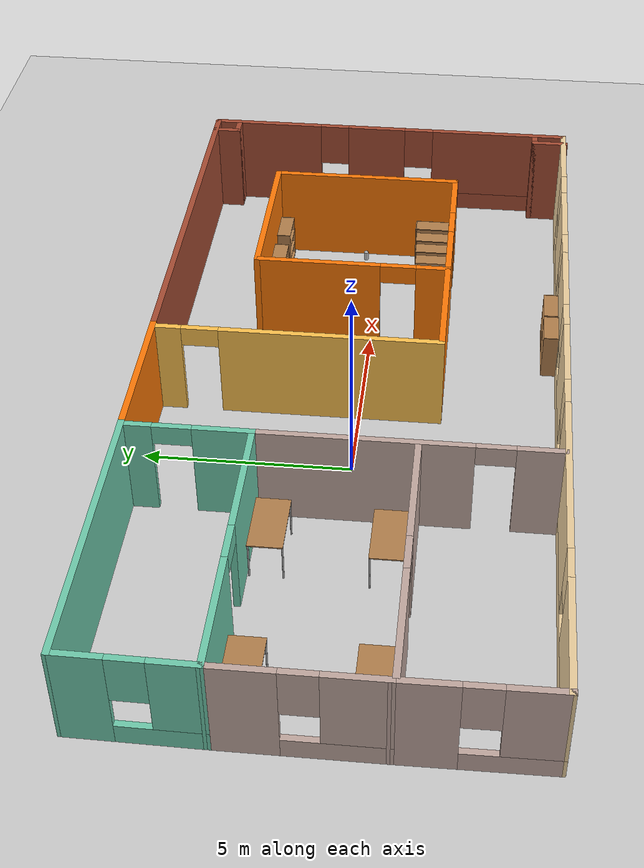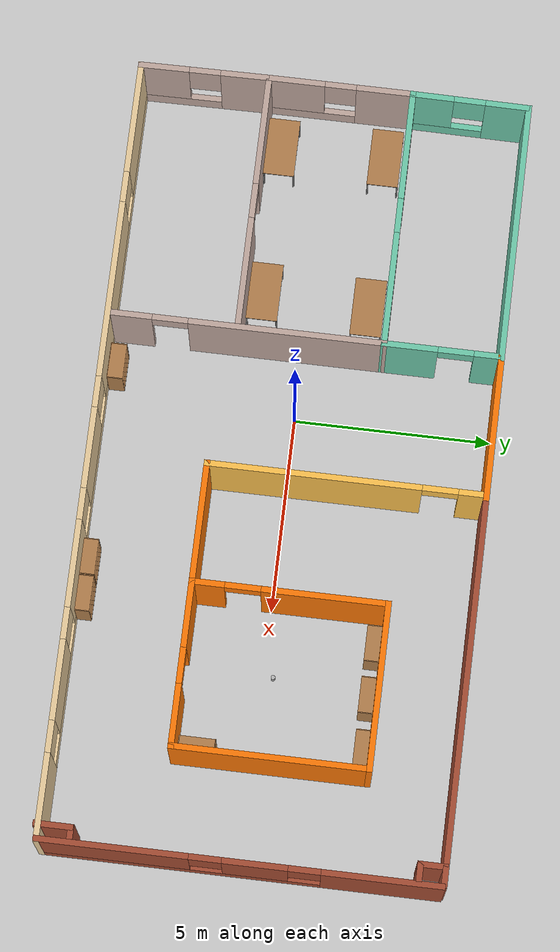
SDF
<sdf version="1.6">
 <world name="default">
  <light name="sun" type="directional">
   <pose>0 0 10 0 -0 0</pose>
   <diffuse>0.8 0.8 0.8 1</diffuse>
   <specular>0.2 0.2 0.2 1</specular>
   <attenuation>
    <range>1000</range>
    <constant>0.9</constant>
    <linear>0.01</linear>
    <quadratic>0.001</quadratic>
   </attenuation>
   <direction>-0.5 0.1 -0.9</direction>
  </light>
  <model name="ground_plane">
   <static>1</static>
   <link name="link">
    <collision name="collision">
     <geometry><plane><normal>0 0 1</normal><size>100 100</size></plane></geometry>
     <surface>
      <contact><collide_bitmask>65535</collide_bitmask></contact>
      <friction><ode><mu>100</mu><mu2>50</mu2></ode></friction>
     </surface>
    </collision>
    <visual name="visual">
     <cast_shadows>0</cast_shadows>
     <geometry><plane><normal>0 0 1</normal><size>100 100</size></plane></geometry>
     <material>
      <script><uri>file://media/materials/scripts/gazebo.material</uri><name>Gazebo/Grey</name></script>
     </material>
    </visual>
   </link>
  </model>
  <gravity>0 0 -9.8</gravity>
  <magnetic_field>6e-06 2.3e-05 -4.2e-05</magnetic_field>
  <atmosphere type="adiabatic"/>
  <physics name="default_physics" default="0" type="ode">
   <max_step_size>0.001</max_step_size>
   <real_time_factor>1</real_time_factor>
   <real_time_update_rate>1000</real_time_update_rate>
  </physics>
  <scene><ambient>0.4 0.4 0.4 1</ambient><background>0.7 0.7 0.7 1</background><shadows>1</shadows></scene>
  <spherical_coordinates>
   <surface_model>EARTH_WGS84</surface_model>
   <latitude_deg>0</latitude_deg>
   <longitude_deg>0</longitude_deg>
   <elevation>0</elevation>
   <heading_deg>0</heading_deg>
  </spherical_coordinates>
  <model name="Some_Building">
   <pose>1.71741 0.02283 0 0 -0 0</pose>
   <link name="Wall_13">
    <pose>3.76972 -1.9787 0 0 -0 0</pose>
    <visual name="Wall_13_Visual_0">
     <pose>-1.25808 0 1.25 0 -0 0</pose>
     <geometry><box><size>4.73385 0.15 2.5</size></box></geometry>
     <material>
      <script><uri>file://media/materials/scripts/gazebo.material</uri><name>Gazebo/Grey</name></script>
      <ambient>0.996078 0.47451 0.0196078 1</ambient>
     </material>
     <meta><layer>0</layer></meta>
    </visual>
    <collision name="Wall_13_Collision_0">
     <geometry><box><size>4.73385 0.15 2.5</size></box></geometry>
     <pose>-1.25808 0 1.25 0 -0 0</pose>
    </collision>
    <visual name="Wall_13_Visual_1">
     <pose>2.81692 0 1.25 0 -0 0</pose>
     <geometry><box><size>1.61615 0.15 2.5</size></box></geometry>
     <material>
      <script><uri>file://media/materials/scripts/gazebo.material</uri><name>Gazebo/Grey</name></script>
      <ambient>0.996078 0.47451 0.0196078 1</ambient>
     </material>
     <meta><layer>0</layer></meta>
    </visual>
    <collision name="Wall_13_Collision_1">
     <geometry><box><size>1.61615 0.15 2.5</size></box></geometry>
     <pose>2.81692 0 1.25 0 -0 0</pose>
    </collision>
    <visual name="Wall_13_Visual_2">
     <pose>1.55885 0 2.25 0 -0 0</pose>
     <geometry><box><size>0.9 0.15 0.5</size></box></geometry>
     <material>
      <script><uri>file://media/materials/scripts/gazebo.material</uri><name>Gazebo/Grey</name></script>
      <ambient>0.996078 0.47451 0.0196078 1</ambient>
     </material>
     <meta><layer>0</layer></meta>
    </visual>
    <collision name="Wall_13_Collision_2">
     <geometry><box><size>0.9 0.15 0.5</size></box></geometry>
     <pose>1.55885 0 2.25 0 -0 0</pose>
    </collision>
   </link>
   <link name="Wall_14">
    <collision name="Wall_14_Collision">
     <geometry><box><size>5 0.15 2.5</size></box></geometry>
     <pose>0 0 1.25 0 -0 0</pose>
    </collision>
    <visual name="Wall_14_Visual">
     <pose>0 0 1.25 0 -0 0</pose>
     <geometry><box><size>5 0.15 2.5</size></box></geometry>
     <material>
      <script><uri>file://media/materials/scripts/gazebo.material</uri><name>Gazebo/Grey</name></script>
      <ambient>0.996078 0.47451 0.0196078 1</ambient>
     </material>
     <meta><layer>0</layer></meta>
    </visual>
    <pose>7.31972 0.446304 0 0 -0 1.5708</pose>
   </link>
   <link name="Wall_15">
    <collision name="Wall_15_Collision">
     <geometry><box><size>4.25 0.15 2.5</size></box></geometry>
     <pose>0 0 1.25 0 -0 0</pose>
    </collision>
    <visual name="Wall_15_Visual">
     <pose>0 0 1.25 0 -0 0</pose>
     <geometry><box><size>4.25 0.15 2.5</size></box></geometry>
     <material>
      <script><uri>file://media/materials/scripts/gazebo.material</uri><name>Gazebo/Grey</name></script>
      <ambient>0.996078 0.47451 0.0196078 1</ambient>
     </material>
     <meta><layer>0</layer></meta>
    </visual>
    <pose>5.26972 2.8713 0 0 -0 3.14159</pose>
   </link>
   <link name="Wall_16">
    <pose>3.21972 0.446304 0 0 0 -1.5708</pose>
    <visual name="Wall_16_Visual_0">
     <pose>-0.891713 0 1.25 0 -0 0</pose>
     <geometry><box><size>3.21657 0.15 2.5</size></box></geometry>
     <material>
      <script><uri>file://media/materials/scripts/gazebo.material</uri><name>Gazebo/Grey</name></script>
      <ambient>0.996078 0.47451 0.0196078 1</ambient>
     </material>
     <meta><layer>0</layer></meta>
    </visual>
    <collision name="Wall_16_Collision_0">
     <geometry><box><size>3.21657 0.15 2.5</size></box></geometry>
     <pose>-0.891713 0 1.25 0 -0 0</pose>
    </collision>
    <visual name="Wall_16_Visual_1">
     <pose>2.05829 0 1.25 0 -0 0</pose>
     <geometry><box><size>0.883427 0.15 2.5</size></box></geometry>
     <material>
      <script><uri>file://media/materials/scripts/gazebo.material</uri><name>Gazebo/Grey</name></script>
      <ambient>0.996078 0.47451 0.0196078 1</ambient>
     </material>
     <meta><layer>0</layer></meta>
    </visual>
    <collision name="Wall_16_Collision_1">
     <geometry><box><size>0.883427 0.15 2.5</size></box></geometry>
     <pose>2.05829 0 1.25 0 -0 0</pose>
    </collision>
    <visual name="Wall_16_Visual_2">
     <pose>1.16657 0 2.25 0 -0 0</pose>
     <geometry><box><size>0.9 0.15 0.5</size></box></geometry>
     <material>
      <script><uri>file://media/materials/scripts/gazebo.material</uri><name>Gazebo/Grey</name></script>
      <ambient>0.996078 0.47451 0.0196078 1</ambient>
     </material>
     <meta><layer>0</layer></meta>
    </visual>
    <collision name="Wall_16_Collision_2">
     <geometry><box><size>0.9 0.15 0.5</size></box></geometry>
     <pose>1.16657 0 2.25 0 -0 0</pose>
    </collision>
   </link>
   <link name="Wall_18">
    <pose>-3.34038 -1.41375 0 0 0 -1.5708</pose>
    <visual name="Wall_18_Visual_0">
     <pose>-1.01152 0 1.25 0 -0 0</pose>
     <geometry><box><size>4.99707 0.15 2.5</size></box></geometry>
     <material>
      <script><uri>file://media/materials/scripts/gazebo.material</uri><name>Gazebo/Grey</name></script>
      <ambient>0.760784 0.662745 0.627451 1</ambient>
     </material>
     <meta><layer>0</layer></meta>
    </visual>
    <collision name="Wall_18_Collision_0">
     <geometry><box><size>4.99707 0.15 2.5</size></box></geometry>
     <pose>-1.01152 0 1.25 0 -0 0</pose>
    </collision>
    <visual name="Wall_18_Visual_1">
     <pose>2.94853 0 1.25 0 -0 0</pose>
     <geometry><box><size>1.12305 0.15 2.5</size></box></geometry>
     <material>
      <script><uri>file://media/materials/scripts/gazebo.material</uri><name>Gazebo/Grey</name></script>
      <ambient>0.760784 0.662745 0.627451 1</ambient>
     </material>
     <meta><layer>0</layer></meta>
    </visual>
    <collision name="Wall_18_Collision_1">
     <geometry><box><size>1.12305 0.15 2.5</size></box></geometry>
     <pose>2.94853 0 1.25 0 -0 0</pose>
    </collision>
    <visual name="Wall_18_Visual_2">
     <pose>1.93701 0 2.25 0 -0 0</pose>
     <geometry><box><size>0.9 0.15 0.5</size></box></geometry>
     <material>
      <script><uri>file://media/materials/scripts/gazebo.material</uri><name>Gazebo/Grey</name></script>
      <ambient>0.760784 0.662745 0.627451 1</ambient>
     </material>
     <meta><layer>0</layer></meta>
    </visual>
    <collision name="Wall_18_Collision_2">
     <geometry><box><size>0.9 0.15 0.5</size></box></geometry>
     <pose>1.93701 0 2.25 0 -0 0</pose>
    </collision>
   </link>
   <link name="Wall_2">
    <pose>9.94117 0.003093 0 0 0 -1.5708</pose>
    <visual name="Wall_2_Visual_0">
     <pose>-3.49485 0 1.25 0 -0 0</pose>
     <geometry><box><size>3.0103 0.15 2.5</size></box></geometry>
     <material>
      <script><uri>file://media/materials/scripts/gazebo.material</uri><name>Gazebo/Bricks</name></script>
      <ambient>1 1 1 1</ambient>
     </material>
     <meta><layer>0</layer></meta>
    </visual>
    <collision name="Wall_2_Collision_0">
     <geometry><box><size>3.0103 0.15 2.5</size></box></geometry>
     <pose>-3.49485 0 1.25 0 -0 0</pose>
    </collision>
    <visual name="Wall_2_Visual_1">
     <pose>1.50515 0 0.25 0 -0 0</pose>
     <geometry><box><size>6.9897 0.15 0.5</size></box></geometry>
     <material>
      <script><uri>file://media/materials/scripts/gazebo.material</uri><name>Gazebo/Bricks</name></script>
      <ambient>1 1 1 1</ambient>
     </material>
     <meta><layer>0</layer></meta>
    </visual>
    <collision name="Wall_2_Collision_1">
     <geometry><box><size>6.9897 0.15 0.5</size></box></geometry>
     <pose>1.50515 0 0.25 0 -0 0</pose>
    </collision>
    <visual name="Wall_2_Visual_2">
     <pose>-0.382884 0 1.5 0 -0 0</pose>
     <geometry><box><size>1.61363 0.15 2</size></box></geometry>
     <material>
      <script><uri>file://media/materials/scripts/gazebo.material</uri><name>Gazebo/Bricks</name></script>
      <ambient>1 1 1 1</ambient>
     </material>
     <meta><layer>0</layer></meta>
    </visual>
    <collision name="Wall_2_Collision_2">
     <geometry><box><size>1.61363 0.15 2</size></box></geometry>
     <pose>-0.382884 0 1.5 0 -0 0</pose>
    </collision>
    <visual name="Wall_2_Visual_3">
     <pose>3.11197 0 1.5 0 -0 0</pose>
     <geometry><box><size>3.77607 0.15 2</size></box></geometry>
     <material>
      <script><uri>file://media/materials/scripts/gazebo.material</uri><name>Gazebo/Bricks</name></script>
      <ambient>1 1 1 1</ambient>
     </material>
     <meta><layer>0</layer></meta>
    </visual>
    <collision name="Wall_2_Collision_3">
     <geometry><box><size>3.77607 0.15 2</size></box></geometry>
     <pose>3.11197 0 1.5 0 -0 0</pose>
    </collision>
    <visual name="Wall_2_Visual_4">
     <pose>-1.5897 0 1.9 0 -0 0</pose>
     <geometry><box><size>0.8 0.15 1.2</size></box></geometry>
     <material>
      <script><uri>file://media/materials/scripts/gazebo.material</uri><name>Gazebo/Bricks</name></script>
      <ambient>1 1 1 1</ambient>
     </material>
     <meta><layer>0</layer></meta>
    </visual>
    <collision name="Wall_2_Collision_4">
     <geometry><box><size>0.8 0.15 1.2</size></box></geometry>
     <pose>-1.5897 0 1.9 0 -0 0</pose>
    </collision>
    <visual name="Wall_2_Visual_5">
     <pose>0.823931 0 1.9 0 -0 0</pose>
     <geometry><box><size>0.8 0.15 1.2</size></box></geometry>
     <material>
      <script><uri>file://media/materials/scripts/gazebo.material</uri><name>Gazebo/Bricks</name></script>
      <ambient>1 1 1 1</ambient>
     </material>
     <meta><layer>0</layer></meta>
    </visual>
    <collision name="Wall_2_Collision_5">
     <geometry><box><size>0.8 0.15 1.2</size></box></geometry>
     <pose>0.823931 0 1.9 0 -0 0</pose>
    </collision>
   </link>
   <link name="Wall_23">
    <pose>-6.65398 -1.65419 0 0 -0 3.14159</pose>
    <visual name="Wall_23_Visual_0">
     <pose>-1.84756 0 1.25 0 -0 0</pose>
     <geometry><box><size>2.80488 0.15 2.5</size></box></geometry>
     <material>
      <script><uri>file://media/materials/scripts/gazebo.material</uri><name>Gazebo/Grey</name></script>
      <ambient>0.760784 0.662745 0.627451 1</ambient>
     </material>
     <meta><layer>0</layer></meta>
    </visual>
    <collision name="Wall_23_Collision_0">
     <geometry><box><size>2.80488 0.15 2.5</size></box></geometry>
     <pose>-1.84756 0 1.25 0 -0 0</pose>
    </collision>
    <visual name="Wall_23_Visual_1">
     <pose>1.85244 0 1.25 0 -0 0</pose>
     <geometry><box><size>2.79512 0.15 2.5</size></box></geometry>
     <material>
      <script><uri>file://media/materials/scripts/gazebo.material</uri><name>Gazebo/Grey</name></script>
      <ambient>0.760784 0.662745 0.627451 1</ambient>
     </material>
     <meta><layer>0</layer></meta>
    </visual>
    <collision name="Wall_23_Collision_1">
     <geometry><box><size>2.79512 0.15 2.5</size></box></geometry>
     <pose>1.85244 0 1.25 0 -0 0</pose>
    </collision>
    <visual name="Wall_23_Visual_2">
     <pose>0.004884 0 2.25 0 -0 0</pose>
     <geometry><box><size>0.9 0.15 0.5</size></box></geometry>
     <material>
      <script><uri>file://media/materials/scripts/gazebo.material</uri><name>Gazebo/Grey</name></script>
      <ambient>0.760784 0.662745 0.627451 1</ambient>
     </material>
     <meta><layer>0</layer></meta>
    </visual>
    <collision name="Wall_23_Collision_2">
     <geometry><box><size>0.9 0.15 0.5</size></box></geometry>
     <pose>0.004884 0 2.25 0 -0 0</pose>
    </collision>
   </link>
   <link name="Wall_27">
    <collision name="Wall_27_Collision">
     <geometry><box><size>6.75 0.15 2.5</size></box></geometry>
     <pose>0 0 1.25 0 -0 0</pose>
    </collision>
    <visual name="Wall_27_Visual">
     <pose>0 0 1.25 0 -0 0</pose>
     <geometry><box><size>6.75 0.15 2.5</size></box></geometry>
     <material>
      <script><uri>file://media/materials/scripts/gazebo.material</uri><name>Gazebo/Grey</name></script>
      <ambient>0.435294 0.796078 0.67451 1</ambient>
     </material>
     <meta><layer>0</layer></meta>
    </visual>
    <pose>-6.60883 4.96832 0 0 -0 0</pose>
   </link>
   <link name="Wall_28">
    <collision name="Wall_28_Collision">
     <geometry><box><size>3.75 0.15 2.5</size></box></geometry>
     <pose>0 0 1.25 0 -0 0</pose>
    </collision>
    <visual name="Wall_28_Visual">
     <pose>0 0 1.25 0 -0 0</pose>
     <geometry><box><size>3.75 0.15 2.5</size></box></geometry>
     <material>
      <script><uri>file://media/materials/scripts/gazebo.material</uri><name>Gazebo/Grey</name></script>
      <ambient>0.996078 0.47451 0.0196078 1</ambient>
     </material>
     <meta><layer>0</layer></meta>
    </visual>
    <pose>-1.50883 4.96832 0 0 -0 0</pose>
   </link>
   <link name="Wall_29">
    <collision name="Wall_29_Collision">
     <geometry><box><size>9.75 0.15 2.5</size></box></geometry>
     <pose>0 0 1.25 0 -0 0</pose>
    </collision>
    <visual name="Wall_29_Visual">
     <pose>0 0 1.25 0 -0 0</pose>
     <geometry><box><size>9.75 0.15 2.5</size></box></geometry>
     <material>
      <script><uri>file://media/materials/scripts/gazebo.material</uri><name>Gazebo/Bricks</name></script>
      <ambient>1 1 1 1</ambient>
     </material>
     <meta><layer>0</layer></meta>
    </visual>
    <pose>5.09117 4.96832 0 0 -0 0</pose>
   </link>
   <link name="Wall_3">
    <pose>0.016175 -4.92191 0 0 -0 3.14159</pose>
    <visual name="Wall_3_Visual_0">
     <pose>-8.91216 0 1.25 0 -0 0</pose>
     <geometry><box><size>2.17568 0.15 2.5</size></box></geometry>
     <material>
      <script><uri>file://media/materials/scripts/gazebo.material</uri><name>Gazebo/Grey</name></script>
      <ambient>0.921569 0.807843 0.615686 1</ambient>
     </material>
     <meta><layer>0</layer></meta>
    </visual>
    <collision name="Wall_3_Collision_0">
     <geometry><box><size>2.17568 0.15 2.5</size></box></geometry>
     <pose>-8.91216 0 1.25 0 -0 0</pose>
    </collision>
    <visual name="Wall_3_Visual_1">
     <pose>1.08784 0 0.25 0 -0 0</pose>
     <geometry><box><size>17.8243 0.15 0.5</size></box></geometry>
     <material>
      <script><uri>file://media/materials/scripts/gazebo.material</uri><name>Gazebo/Grey</name></script>
      <ambient>0.921569 0.807843 0.615686 1</ambient>
     </material>
     <meta><layer>0</layer></meta>
    </visual>
    <collision name="Wall_3_Collision_1">
     <geometry><box><size>17.8243 0.15 0.5</size></box></geometry>
     <pose>1.08784 0 0.25 0 -0 0</pose>
    </collision>
    <visual name="Wall_3_Visual_2">
     <pose>-6.01637 0 1.5 0 -0 0</pose>
     <geometry><box><size>2.0159 0.15 2</size></box></geometry>
     <material>
      <script><uri>file://media/materials/scripts/gazebo.material</uri><name>Gazebo/Grey</name></script>
      <ambient>0.921569 0.807843 0.615686 1</ambient>
     </material>
     <meta><layer>0</layer></meta>
    </visual>
    <collision name="Wall_3_Collision_2">
     <geometry><box><size>2.0159 0.15 2</size></box></geometry>
     <pose>-6.01637 0 1.5 0 -0 0</pose>
    </collision>
    <visual name="Wall_3_Visual_3">
     <pose>-3.0999 0 1.5 0 -0 0</pose>
     <geometry><box><size>2.21704 0.15 2</size></box></geometry>
     <material>
      <script><uri>file://media/materials/scripts/gazebo.material</uri><name>Gazebo/Grey</name></script>
      <ambient>0.921569 0.807843 0.615686 1</ambient>
     </material>
     <meta><layer>0</layer></meta>
    </visual>
    <collision name="Wall_3_Collision_3">
     <geometry><box><size>2.21704 0.15 2</size></box></geometry>
     <pose>-3.0999 0 1.5 0 -0 0</pose>
    </collision>
    <visual name="Wall_3_Visual_4">
     <pose>-0.153265 0 1.5 0 -0 0</pose>
     <geometry><box><size>2.07624 0.15 2</size></box></geometry>
     <material>
      <script><uri>file://media/materials/scripts/gazebo.material</uri><name>Gazebo/Grey</name></script>
      <ambient>0.921569 0.807843 0.615686 1</ambient>
     </material>
     <meta><layer>0</layer></meta>
    </visual>
    <collision name="Wall_3_Collision_4">
     <geometry><box><size>2.07624 0.15 2</size></box></geometry>
     <pose>-0.153265 0 1.5 0 -0 0</pose>
    </collision>
    <visual name="Wall_3_Visual_5">
     <pose>3.97002 0 1.5 0 -0 0</pose>
     <geometry><box><size>4.57032 0.15 2</size></box></geometry>
     <material>
      <script><uri>file://media/materials/scripts/gazebo.material</uri><name>Gazebo/Grey</name></script>
      <ambient>0.921569 0.807843 0.615686 1</ambient>
     </material>
     <meta><layer>0</layer></meta>
    </visual>
    <collision name="Wall_3_Collision_5">
     <geometry><box><size>4.57032 0.15 2</size></box></geometry>
     <pose>3.97002 0 1.5 0 -0 0</pose>
    </collision>
    <visual name="Wall_3_Visual_6">
     <pose>8.52759 0 1.5 0 -0 0</pose>
     <geometry><box><size>2.94482 0.15 2</size></box></geometry>
     <material>
      <script><uri>file://media/materials/scripts/gazebo.material</uri><name>Gazebo/Grey</name></script>
      <ambient>0.921569 0.807843 0.615686 1</ambient>
     </material>
     <meta><layer>0</layer></meta>
    </visual>
    <collision name="Wall_3_Collision_6">
     <geometry><box><size>2.94482 0.15 2</size></box></geometry>
     <pose>8.52759 0 1.5 0 -0 0</pose>
    </collision>
    <visual name="Wall_3_Visual_7">
     <pose>-7.42432 0 1.9 0 -0 0</pose>
     <geometry><box><size>0.8 0.15 1.2</size></box></geometry>
     <material>
      <script><uri>file://media/materials/scripts/gazebo.material</uri><name>Gazebo/Grey</name></script>
      <ambient>0.921569 0.807843 0.615686 1</ambient>
     </material>
     <meta><layer>0</layer></meta>
    </visual>
    <collision name="Wall_3_Collision_7">
     <geometry><box><size>0.8 0.15 1.2</size></box></geometry>
     <pose>-7.42432 0 1.9 0 -0 0</pose>
    </collision>
    <visual name="Wall_3_Visual_8">
     <pose>-4.60842 0 1.9 0 -0 0</pose>
     <geometry><box><size>0.8 0.15 1.2</size></box></geometry>
     <material>
      <script><uri>file://media/materials/scripts/gazebo.material</uri><name>Gazebo/Grey</name></script>
      <ambient>0.921569 0.807843 0.615686 1</ambient>
     </material>
     <meta><layer>0</layer></meta>
    </visual>
    <collision name="Wall_3_Collision_8">
     <geometry><box><size>0.8 0.15 1.2</size></box></geometry>
     <pose>-4.60842 0 1.9 0 -0 0</pose>
    </collision>
    <visual name="Wall_3_Visual_9">
     <pose>-1.59139 0 1.9 0 -0 0</pose>
     <geometry><box><size>0.8 0.15 1.2</size></box></geometry>
     <material>
      <script><uri>file://media/materials/scripts/gazebo.material</uri><name>Gazebo/Grey</name></script>
      <ambient>0.921569 0.807843 0.615686 1</ambient>
     </material>
     <meta><layer>0</layer></meta>
    </visual>
    <collision name="Wall_3_Collision_9">
     <geometry><box><size>0.8 0.15 1.2</size></box></geometry>
     <pose>-1.59139 0 1.9 0 -0 0</pose>
    </collision>
    <visual name="Wall_3_Visual_10">
     <pose>1.28486 0 1.9 0 -0 0</pose>
     <geometry><box><size>0.8 0.15 1.2</size></box></geometry>
     <material>
      <script><uri>file://media/materials/scripts/gazebo.material</uri><name>Gazebo/Grey</name></script>
      <ambient>0.921569 0.807843 0.615686 1</ambient>
     </material>
     <meta><layer>0</layer></meta>
    </visual>
    <collision name="Wall_3_Collision_10">
     <geometry><box><size>0.8 0.15 1.2</size></box></geometry>
     <pose>1.28486 0 1.9 0 -0 0</pose>
    </collision>
    <visual name="Wall_3_Visual_11">
     <pose>6.65518 0 1.9 0 -0 0</pose>
     <geometry><box><size>0.8 0.15 1.2</size></box></geometry>
     <material>
      <script><uri>file://media/materials/scripts/gazebo.material</uri><name>Gazebo/Grey</name></script>
      <ambient>0.921569 0.807843 0.615686 1</ambient>
     </material>
     <meta><layer>0</layer></meta>
    </visual>
    <collision name="Wall_3_Collision_11">
     <geometry><box><size>0.8 0.15 1.2</size></box></geometry>
     <pose>6.65518 0 1.9 0 -0 0</pose>
    </collision>
   </link>
   <link name="Wall_31">
    <pose>-9.9246 3.49345 0 0 0 -1.58149</pose>
    <visual name="Wall_31_Visual_0">
     <pose>-0.962755 0 1.25 0 -0 0</pose>
     <geometry><box><size>1.1744 0.15 2.5</size></box></geometry>
     <material>
      <script><uri>file://media/materials/scripts/gazebo.material</uri><name>Gazebo/Grey</name></script>
      <ambient>0.435294 0.796078 0.67451 1</ambient>
     </material>
     <meta><layer>0</layer></meta>
    </visual>
    <collision name="Wall_31_Collision_0">
     <geometry><box><size>1.1744 0.15 2.5</size></box></geometry>
     <pose>-0.962755 0 1.25 0 -0 0</pose>
    </collision>
    <visual name="Wall_31_Visual_1">
     <pose>0.587199 0 0.25 0 -0 0</pose>
     <geometry><box><size>1.92551 0.15 0.5</size></box></geometry>
     <material>
      <script><uri>file://media/materials/scripts/gazebo.material</uri><name>Gazebo/Grey</name></script>
      <ambient>0.435294 0.796078 0.67451 1</ambient>
     </material>
     <meta><layer>0</layer></meta>
    </visual>
    <collision name="Wall_31_Collision_1">
     <geometry><box><size>1.92551 0.15 0.5</size></box></geometry>
     <pose>0.587199 0 0.25 0 -0 0</pose>
    </collision>
    <visual name="Wall_31_Visual_2">
     <pose>0.987199 0 1.5 0 -0 0</pose>
     <geometry><box><size>1.12551 0.15 2</size></box></geometry>
     <material>
      <script><uri>file://media/materials/scripts/gazebo.material</uri><name>Gazebo/Grey</name></script>
      <ambient>0.435294 0.796078 0.67451 1</ambient>
     </material>
     <meta><layer>0</layer></meta>
    </visual>
    <collision name="Wall_31_Collision_2">
     <geometry><box><size>1.12551 0.15 2</size></box></geometry>
     <pose>0.987199 0 1.5 0 -0 0</pose>
    </collision>
    <visual name="Wall_31_Visual_3">
     <pose>0.024445 0 1.9 0 -0 0</pose>
     <geometry><box><size>0.8 0.15 1.2</size></box></geometry>
     <material>
      <script><uri>file://media/materials/scripts/gazebo.material</uri><name>Gazebo/Grey</name></script>
      <ambient>0.435294 0.796078 0.67451 1</ambient>
     </material>
     <meta><layer>0</layer></meta>
    </visual>
    <collision name="Wall_31_Collision_3">
     <geometry><box><size>0.8 0.15 1.2</size></box></geometry>
     <pose>0.024445 0 1.9 0 -0 0</pose>
    </collision>
   </link>
   <link name="Wall_35">
    <pose>-9.94038 0.218581 0 0 0 -1.5708</pose>
    <visual name="Wall_35_Visual_0">
     <pose>-1.11653 0 1.25 0 -0 0</pose>
     <geometry><box><size>1.51695 0.15 2.5</size></box></geometry>
     <material>
      <script><uri>file://media/materials/scripts/gazebo.material</uri><name>Gazebo/Grey</name></script>
      <ambient>0.760784 0.662745 0.627451 1</ambient>
     </material>
     <meta><layer>0</layer></meta>
    </visual>
    <collision name="Wall_35_Collision_0">
     <geometry><box><size>1.51695 0.15 2.5</size></box></geometry>
     <pose>-1.11653 0 1.25 0 -0 0</pose>
    </collision>
    <visual name="Wall_35_Visual_1">
     <pose>0.758474 0 0.25 0 -0 0</pose>
     <geometry><box><size>2.23305 0.15 0.5</size></box></geometry>
     <material>
      <script><uri>file://media/materials/scripts/gazebo.material</uri><name>Gazebo/Grey</name></script>
      <ambient>0.760784 0.662745 0.627451 1</ambient>
     </material>
     <meta><layer>0</layer></meta>
    </visual>
    <collision name="Wall_35_Collision_1">
     <geometry><box><size>2.23305 0.15 0.5</size></box></geometry>
     <pose>0.758474 0 0.25 0 -0 0</pose>
    </collision>
    <visual name="Wall_35_Visual_2">
     <pose>1.15847 0 1.5 0 -0 0</pose>
     <geometry><box><size>1.43305 0.15 2</size></box></geometry>
     <material>
      <script><uri>file://media/materials/scripts/gazebo.material</uri><name>Gazebo/Grey</name></script>
      <ambient>0.760784 0.662745 0.627451 1</ambient>
     </material>
     <meta><layer>0</layer></meta>
    </visual>
    <collision name="Wall_35_Collision_2">
     <geometry><box><size>1.43305 0.15 2</size></box></geometry>
     <pose>1.15847 0 1.5 0 -0 0</pose>
    </collision>
    <visual name="Wall_35_Visual_3">
     <pose>0.041948 0 1.9 0 -0 0</pose>
     <geometry><box><size>0.8 0.15 1.2</size></box></geometry>
     <material>
      <script><uri>file://media/materials/scripts/gazebo.material</uri><name>Gazebo/Grey</name></script>
      <ambient>0.760784 0.662745 0.627451 1</ambient>
     </material>
     <meta><layer>0</layer></meta>
    </visual>
    <collision name="Wall_35_Collision_3">
     <geometry><box><size>0.8 0.15 1.2</size></box></geometry>
     <pose>0.041948 0 1.9 0 -0 0</pose>
    </collision>
   </link>
   <link name="Wall_39">
    <pose>-9.9246 -3.25166 0 0 0 -1.56135</pose>
    <visual name="Wall_39_Visual_0">
     <pose>-1.0531 0 1.25 0 -0 0</pose>
     <geometry><box><size>1.38444 0.15 2.5</size></box></geometry>
     <material>
      <script><uri>file://media/materials/scripts/gazebo.material</uri><name>Gazebo/Grey</name></script>
      <ambient>0.760784 0.662745 0.627451 1</ambient>
     </material>
     <meta><layer>0</layer></meta>
    </visual>
    <collision name="Wall_39_Collision_0">
     <geometry><box><size>1.38444 0.15 2.5</size></box></geometry>
     <pose>-1.0531 0 1.25 0 -0 0</pose>
    </collision>
    <visual name="Wall_39_Visual_1">
     <pose>0.69222 0 0.25 0 -0 0</pose>
     <geometry><box><size>2.1062 0.15 0.5</size></box></geometry>
     <material>
      <script><uri>file://media/materials/scripts/gazebo.material</uri><name>Gazebo/Grey</name></script>
      <ambient>0.760784 0.662745 0.627451 1</ambient>
     </material>
     <meta><layer>0</layer></meta>
    </visual>
    <collision name="Wall_39_Collision_1">
     <geometry><box><size>2.1062 0.15 0.5</size></box></geometry>
     <pose>0.69222 0 0.25 0 -0 0</pose>
    </collision>
    <visual name="Wall_39_Visual_2">
     <pose>1.09222 0 1.5 0 -0 0</pose>
     <geometry><box><size>1.3062 0.15 2</size></box></geometry>
     <material>
      <script><uri>file://media/materials/scripts/gazebo.material</uri><name>Gazebo/Grey</name></script>
      <ambient>0.760784 0.662745 0.627451 1</ambient>
     </material>
     <meta><layer>0</layer></meta>
    </visual>
    <collision name="Wall_39_Collision_2">
     <geometry><box><size>1.3062 0.15 2</size></box></geometry>
     <pose>1.09222 0 1.5 0 -0 0</pose>
    </collision>
    <visual name="Wall_39_Visual_3">
     <pose>0.039122 0 1.9 0 -0 0</pose>
     <geometry><box><size>0.8 0.15 1.2</size></box></geometry>
     <material>
      <script><uri>file://media/materials/scripts/gazebo.material</uri><name>Gazebo/Grey</name></script>
      <ambient>0.760784 0.662745 0.627451 1</ambient>
     </material>
     <meta><layer>0</layer></meta>
    </visual>
    <collision name="Wall_39_Collision_3">
     <geometry><box><size>0.8 0.15 1.2</size></box></geometry>
     <pose>0.039122 0 1.9 0 -0 0</pose>
    </collision>
   </link>
   <link name="Wall_41">
    <collision name="Wall_41_Collision">
     <geometry><box><size>0.75 0.15 2.5</size></box></geometry>
     <pose>0 0 1.25 0 -0 0</pose>
    </collision>
    <visual name="Wall_41_Visual">
     <pose>0 0 1.25 0 -0 0</pose>
     <geometry><box><size>0.75 0.15 2.5</size></box></geometry>
     <material>
      <script><uri>file://media/materials/scripts/gazebo.material</uri><name>Gazebo/Bricks</name></script>
      <ambient>1 1 1 1</ambient>
     </material>
     <meta><layer>0</layer></meta>
    </visual>
    <pose>9.46317 4.64808 0 0 0 -1.5708</pose>
   </link>
   <link name="Wall_42">
    <collision name="Wall_42_Collision">
     <geometry><box><size>0.5 0.15 2.5</size></box></geometry>
     <pose>0 0 1.25 0 -0 0</pose>
    </collision>
    <visual name="Wall_42_Visual">
     <pose>0 0 1.25 0 -0 0</pose>
     <geometry><box><size>0.5 0.15 2.5</size></box></geometry>
     <material>
      <script><uri>file://media/materials/scripts/gazebo.material</uri><name>Gazebo/Bricks</name></script>
      <ambient>1 1 1 1</ambient>
     </material>
     <meta><layer>0</layer></meta>
    </visual>
    <pose>9.63817 4.34808 0 0 -0 0</pose>
   </link>
   <link name="Wall_45">
    <collision name="Wall_45_Collision">
     <geometry><box><size>0.5 0.15 2.5</size></box></geometry>
     <pose>0 0 1.25 0 -0 0</pose>
    </collision>
    <visual name="Wall_45_Visual">
     <pose>0 0 1.25 0 -0 0</pose>
     <geometry><box><size>0.5 0.15 2.5</size></box></geometry>
     <material>
      <script><uri>file://media/materials/scripts/gazebo.material</uri><name>Gazebo/Bricks</name></script>
      <ambient>1 1 1 1</ambient>
     </material>
     <meta><layer>0</layer></meta>
    </visual>
    <pose>9.75078 -4.11912 0 0 -0 3.14159</pose>
   </link>
   <link name="Wall_46">
    <collision name="Wall_46_Collision">
     <geometry><box><size>1 0.15 2.5</size></box></geometry>
     <pose>0 0 1.25 0 -0 0</pose>
    </collision>
    <visual name="Wall_46_Visual">
     <pose>0 0 1.25 0 -0 0</pose>
     <geometry><box><size>1 0.15 2.5</size></box></geometry>
     <material>
      <script><uri>file://media/materials/scripts/gazebo.material</uri><name>Gazebo/Bricks</name></script>
      <ambient>1 1 1 1</ambient>
     </material>
     <meta><layer>0</layer></meta>
    </visual>
    <pose>9.57578 -4.54412 0 0 0 -1.5708</pose>
   </link>
   <link name="Wall_5">
    <pose>-3.34038 3.4463 0 0 0 -1.5708</pose>
    <visual name="Wall_5_Visual_0">
     <pose>-1.16455 0 1.25 0 -0 0</pose>
     <geometry><box><size>0.670906 0.15 2.5</size></box></geometry>
     <material>
      <script><uri>file://media/materials/scripts/gazebo.material</uri><name>Gazebo/Grey</name></script>
      <ambient>0.435294 0.796078 0.67451 1</ambient>
     </material>
     <meta><layer>0</layer></meta>
    </visual>
    <collision name="Wall_5_Collision_0">
     <geometry><box><size>0.670906 0.15 2.5</size></box></geometry>
     <pose>-1.16455 0 1.25 0 -0 0</pose>
    </collision>
    <visual name="Wall_5_Visual_1">
     <pose>0.785453 0 1.25 0 -0 0</pose>
     <geometry><box><size>1.42909 0.15 2.5</size></box></geometry>
     <material>
      <script><uri>file://media/materials/scripts/gazebo.material</uri><name>Gazebo/Grey</name></script>
      <ambient>0.435294 0.796078 0.67451 1</ambient>
     </material>
     <meta><layer>0</layer></meta>
    </visual>
    <collision name="Wall_5_Collision_1">
     <geometry><box><size>1.42909 0.15 2.5</size></box></geometry>
     <pose>0.785453 0 1.25 0 -0 0</pose>
    </collision>
    <visual name="Wall_5_Visual_2">
     <pose>-0.379094 0 2.25 0 -0 0</pose>
     <geometry><box><size>0.9 0.15 0.5</size></box></geometry>
     <material>
      <script><uri>file://media/materials/scripts/gazebo.material</uri><name>Gazebo/Grey</name></script>
      <ambient>0.435294 0.796078 0.67451 1</ambient>
     </material>
     <meta><layer>0</layer></meta>
    </visual>
    <collision name="Wall_5_Collision_2">
     <geometry><box><size>0.9 0.15 0.5</size></box></geometry>
     <pose>-0.379094 0 2.25 0 -0 0</pose>
    </collision>
   </link>
   <link name="Wall_6">
    <pose>-6.64038 2.01994 0 0 0 -3.14118</pose>
    <visual name="Wall_6_Visual_0">
     <pose>-1.88302 0 1.25 0 -0 0</pose>
     <geometry><box><size>2.98397 0.15 2.5</size></box></geometry>
     <material>
      <script><uri>file://media/materials/scripts/gazebo.material</uri><name>Gazebo/Grey</name></script>
      <ambient>0.435294 0.796078 0.67451 1</ambient>
     </material>
     <meta><layer>0</layer></meta>
    </visual>
    <collision name="Wall_6_Collision_0">
     <geometry><box><size>2.98397 0.15 2.5</size></box></geometry>
     <pose>-1.88302 0 1.25 0 -0 0</pose>
    </collision>
    <visual name="Wall_6_Visual_1">
     <pose>1.94198 0 1.25 0 -0 0</pose>
     <geometry><box><size>2.86603 0.15 2.5</size></box></geometry>
     <material>
      <script><uri>file://media/materials/scripts/gazebo.material</uri><name>Gazebo/Grey</name></script>
      <ambient>0.435294 0.796078 0.67451 1</ambient>
     </material>
     <meta><layer>0</layer></meta>
    </visual>
    <collision name="Wall_6_Collision_1">
     <geometry><box><size>2.86603 0.15 2.5</size></box></geometry>
     <pose>1.94198 0 1.25 0 -0 0</pose>
    </collision>
    <visual name="Wall_6_Visual_2">
     <pose>0.058966 0 2.25 0 -0 0</pose>
     <geometry><box><size>0.9 0.15 0.5</size></box></geometry>
     <material>
      <script><uri>file://media/materials/scripts/gazebo.material</uri><name>Gazebo/Grey</name></script>
      <ambient>0.435294 0.796078 0.67451 1</ambient>
     </material>
     <meta><layer>0</layer></meta>
    </visual>
    <collision name="Wall_6_Collision_2">
     <geometry><box><size>0.9 0.15 0.5</size></box></geometry>
     <pose>0.058966 0 2.25 0 -0 0</pose>
    </collision>
   </link>
   <link name="Wall_9">
    <pose>0.219724 1.4463 0 0 0 -1.5708</pose>
    <visual name="Wall_9_Visual_0">
     <pose>-3.16455 0 1.25 0 -0 0</pose>
     <geometry><box><size>0.670906 0.15 2.5</size></box></geometry>
     <material>
      <script><uri>file://media/materials/scripts/gazebo.material</uri><name>Gazebo/Grey</name></script>
      <ambient>1 0.764706 0.305882 1</ambient>
     </material>
     <meta><layer>0</layer></meta>
    </visual>
    <collision name="Wall_9_Collision_0">
     <geometry><box><size>0.670906 0.15 2.5</size></box></geometry>
     <pose>-3.16455 0 1.25 0 -0 0</pose>
    </collision>
    <visual name="Wall_9_Visual_1">
     <pose>0.785453 0 1.25 0 -0 0</pose>
     <geometry><box><size>5.42909 0.15 2.5</size></box></geometry>
     <material>
      <script><uri>file://media/materials/scripts/gazebo.material</uri><name>Gazebo/Grey</name></script>
      <ambient>1 0.764706 0.305882 1</ambient>
     </material>
     <meta><layer>0</layer></meta>
    </visual>
    <collision name="Wall_9_Collision_1">
     <geometry><box><size>5.42909 0.15 2.5</size></box></geometry>
     <pose>0.785453 0 1.25 0 -0 0</pose>
    </collision>
    <visual name="Wall_9_Visual_2">
     <pose>-2.37909 0 2.25 0 -0 0</pose>
     <geometry><box><size>0.9 0.15 0.5</size></box></geometry>
     <material>
      <script><uri>file://media/materials/scripts/gazebo.material</uri><name>Gazebo/Grey</name></script>
      <ambient>1 0.764706 0.305882 1</ambient>
     </material>
     <meta><layer>0</layer></meta>
    </visual>
    <collision name="Wall_9_Collision_2">
     <geometry><box><size>0.9 0.15 0.5</size></box></geometry>
     <pose>-2.37909 0 2.25 0 -0 0</pose>
    </collision>
   </link>
   <static>1</static>
  </model>
  <model name="bookshelf">
   <static>1</static>
   <link name="link">
    <inertial><mass>1</mass></inertial>
    <collision name="back">
     <pose>0 0.005 0.6 0 -0 0</pose>
     <geometry><box><size>0.9 0.01 1.2</size></box></geometry>
    </collision>
    <visual name="visual1">
     <pose>0 0.005 0.6 0 -0 0</pose>
     <geometry><box><size>0.9 0.01 1.2</size></box></geometry>
     <material>
      <script><uri>file://media/materials/scripts/gazebo.material</uri><name>Gazebo/Wood</name></script>
     </material>
    </visual>
    <collision name="left_side">
     <pose>0.45 -0.195 0.6 0 -0 0</pose>
     <geometry><box><size>0.02 0.4 1.2</size></box></geometry>
    </collision>
    <visual name="visual2">
     <pose>0.45 -0.195 0.6 0 -0 0</pose>
     <geometry><box><size>0.02 0.4 1.2</size></box></geometry>
     <material>
      <script><uri>file://media/materials/scripts/gazebo.material</uri><name>Gazebo/Wood</name></script>
     </material>
    </visual>
    <collision name="right_side">
     <pose>-0.45 -0.195 0.6 0 -0 0</pose>
     <geometry><box><size>0.02 0.4 1.2</size></box></geometry>
    </collision>
    <visual name="visual3">
     <pose>-0.45 -0.195 0.6 0 -0 0</pose>
     <geometry><box><size>0.02 0.4 1.2</size></box></geometry>
     <material>
      <script><uri>file://media/materials/scripts/gazebo.material</uri><name>Gazebo/Wood</name></script>
     </material>
    </visual>
    <collision name="bottom">
     <pose>0 -0.195 0.03 0 -0 0</pose>
     <geometry><box><size>0.88 0.4 0.06</size></box></geometry>
    </collision>
    <visual name="visual4">
     <pose>0 -0.195 0.03 0 -0 0</pose>
     <geometry><box><size>0.88 0.4 0.06</size></box></geometry>
     <material>
      <script><uri>file://media/materials/scripts/gazebo.material</uri><name>Gazebo/Wood</name></script>
     </material>
    </visual>
    <collision name="top">
     <pose>0 -0.195 1.19 0 -0 0</pose>
     <geometry><box><size>0.88 0.4 0.02</size></box></geometry>
    </collision>
    <visual name="visual5">
     <pose>0 -0.195 1.19 0 -0 0</pose>
     <geometry><box><size>0.88 0.4 0.02</size></box></geometry>
     <material>
      <script><uri>file://media/materials/scripts/gazebo.material</uri><name>Gazebo/Wood</name></script>
     </material>
    </visual>
    <collision name="low_shelf">
     <pose>0 -0.195 0.43 0 -0 0</pose>
     <geometry><box><size>0.88 0.4 0.02</size></box></geometry>
    </collision>
    <visual name="visual6">
     <pose>0 -0.195 0.43 0 -0 0</pose>
     <geometry><box><size>0.88 0.4 0.02</size></box></geometry>
     <material>
      <script><uri>file://media/materials/scripts/gazebo.material</uri><name>Gazebo/Wood</name></script>
     </material>
    </visual>
    <collision name="high_shelf">
     <pose>0 -0.195 0.8 0 -0 0</pose>
     <geometry><box><size>0.88 0.4 0.02</size></box></geometry>
    </collision>
    <visual name="visual7">
     <pose>0 -0.195 0.8 0 -0 0</pose>
     <geometry><box><size>0.88 0.4 0.02</size></box></geometry>
     <material>
      <script><uri>file://media/materials/scripts/gazebo.material</uri><name>Gazebo/Wood</name></script>
     </material>
    </visual>
   </link>
   <pose>5.70821 2.84293 0 0 -0 0</pose>
  </model>
  <model name="bookshelf_0">
   <static>1</static>
   <link name="link">
    <inertial><mass>1</mass></inertial>
    <collision name="back">
     <pose>0 0.005 0.6 0 -0 0</pose>
     <geometry><box><size>0.9 0.01 1.2</size></box></geometry>
    </collision>
    <visual name="visual1">
     <pose>0 0.005 0.6 0 -0 0</pose>
     <geometry><box><size>0.9 0.01 1.2</size></box></geometry>
     <material>
      <script><uri>file://media/materials/scripts/gazebo.material</uri><name>Gazebo/Wood</name></script>
     </material>
    </visual>
    <collision name="left_side">
     <pose>0.45 -0.195 0.6 0 -0 0</pose>
     <geometry><box><size>0.02 0.4 1.2</size></box></geometry>
    </collision>
    <visual name="visual2">
     <pose>0.45 -0.195 0.6 0 -0 0</pose>
     <geometry><box><size>0.02 0.4 1.2</size></box></geometry>
     <material>
      <script><uri>file://media/materials/scripts/gazebo.material</uri><name>Gazebo/Wood</name></script>
     </material>
    </visual>
    <collision name="right_side">
     <pose>-0.45 -0.195 0.6 0 -0 0</pose>
     <geometry><box><size>0.02 0.4 1.2</size></box></geometry>
    </collision>
    <visual name="visual3">
     <pose>-0.45 -0.195 0.6 0 -0 0</pose>
     <geometry><box><size>0.02 0.4 1.2</size></box></geometry>
     <material>
      <script><uri>file://media/materials/scripts/gazebo.material</uri><name>Gazebo/Wood</name></script>
     </material>
    </visual>
    <collision name="bottom">
     <pose>0 -0.195 0.03 0 -0 0</pose>
     <geometry><box><size>0.88 0.4 0.06</size></box></geometry>
    </collision>
    <visual name="visual4">
     <pose>0 -0.195 0.03 0 -0 0</pose>
     <geometry><box><size>0.88 0.4 0.06</size></box></geometry>
     <material>
      <script><uri>file://media/materials/scripts/gazebo.material</uri><name>Gazebo/Wood</name></script>
     </material>
    </visual>
    <collision name="top">
     <pose>0 -0.195 1.19 0 -0 0</pose>
     <geometry><box><size>0.88 0.4 0.02</size></box></geometry>
    </collision>
    <visual name="visual5">
     <pose>0 -0.195 1.19 0 -0 0</pose>
     <geometry><box><size>0.88 0.4 0.02</size></box></geometry>
     <material>
      <script><uri>file://media/materials/scripts/gazebo.material</uri><name>Gazebo/Wood</name></script>
     </material>
    </visual>
    <collision name="low_shelf">
     <pose>0 -0.195 0.43 0 -0 0</pose>
     <geometry><box><size>0.88 0.4 0.02</size></box></geometry>
    </collision>
    <visual name="visual6">
     <pose>0 -0.195 0.43 0 -0 0</pose>
     <geometry><box><size>0.88 0.4 0.02</size></box></geometry>
     <material>
      <script><uri>file://media/materials/scripts/gazebo.material</uri><name>Gazebo/Wood</name></script>
     </material>
    </visual>
    <collision name="high_shelf">
     <pose>0 -0.195 0.8 0 -0 0</pose>
     <geometry><box><size>0.88 0.4 0.02</size></box></geometry>
    </collision>
    <visual name="visual7">
     <pose>0 -0.195 0.8 0 -0 0</pose>
     <geometry><box><size>0.88 0.4 0.02</size></box></geometry>
     <material>
      <script><uri>file://media/materials/scripts/gazebo.material</uri><name>Gazebo/Wood</name></script>
     </material>
    </visual>
   </link>
   <pose>7.01255 2.84092 0 0 -0 0</pose>
  </model>
  <model name="bookshelf_1">
   <static>1</static>
   <link name="link">
    <inertial><mass>1</mass></inertial>
    <collision name="back">
     <pose>0 0.005 0.6 0 -0 0</pose>
     <geometry><box><size>0.9 0.01 1.2</size></box></geometry>
    </collision>
    <visual name="visual1">
     <pose>0 0.005 0.6 0 -0 0</pose>
     <geometry><box><size>0.9 0.01 1.2</size></box></geometry>
     <material>
      <script><uri>file://media/materials/scripts/gazebo.material</uri><name>Gazebo/Wood</name></script>
     </material>
    </visual>
    <collision name="left_side">
     <pose>0.45 -0.195 0.6 0 -0 0</pose>
     <geometry><box><size>0.02 0.4 1.2</size></box></geometry>
    </collision>
    <visual name="visual2">
     <pose>0.45 -0.195 0.6 0 -0 0</pose>
     <geometry><box><size>0.02 0.4 1.2</size></box></geometry>
     <material>
      <script><uri>file://media/materials/scripts/gazebo.material</uri><name>Gazebo/Wood</name></script>
     </material>
    </visual>
    <collision name="right_side">
     <pose>-0.45 -0.195 0.6 0 -0 0</pose>
     <geometry><box><size>0.02 0.4 1.2</size></box></geometry>
    </collision>
    <visual name="visual3">
     <pose>-0.45 -0.195 0.6 0 -0 0</pose>
     <geometry><box><size>0.02 0.4 1.2</size></box></geometry>
     <material>
      <script><uri>file://media/materials/scripts/gazebo.material</uri><name>Gazebo/Wood</name></script>
     </material>
    </visual>
    <collision name="bottom">
     <pose>0 -0.195 0.03 0 -0 0</pose>
     <geometry><box><size>0.88 0.4 0.06</size></box></geometry>
    </collision>
    <visual name="visual4">
     <pose>0 -0.195 0.03 0 -0 0</pose>
     <geometry><box><size>0.88 0.4 0.06</size></box></geometry>
     <material>
      <script><uri>file://media/materials/scripts/gazebo.material</uri><name>Gazebo/Wood</name></script>
     </material>
    </visual>
    <collision name="top">
     <pose>0 -0.195 1.19 0 -0 0</pose>
     <geometry><box><size>0.88 0.4 0.02</size></box></geometry>
    </collision>
    <visual name="visual5">
     <pose>0 -0.195 1.19 0 -0 0</pose>
     <geometry><box><size>0.88 0.4 0.02</size></box></geometry>
     <material>
      <script><uri>file://media/materials/scripts/gazebo.material</uri><name>Gazebo/Wood</name></script>
     </material>
    </visual>
    <collision name="low_shelf">
     <pose>0 -0.195 0.43 0 -0 0</pose>
     <geometry><box><size>0.88 0.4 0.02</size></box></geometry>
    </collision>
    <visual name="visual6">
     <pose>0 -0.195 0.43 0 -0 0</pose>
     <geometry><box><size>0.88 0.4 0.02</size></box></geometry>
     <material>
      <script><uri>file://media/materials/scripts/gazebo.material</uri><name>Gazebo/Wood</name></script>
     </material>
    </visual>
    <collision name="high_shelf">
     <pose>0 -0.195 0.8 0 -0 0</pose>
     <geometry><box><size>0.88 0.4 0.02</size></box></geometry>
    </collision>
    <visual name="visual7">
     <pose>0 -0.195 0.8 0 -0 0</pose>
     <geometry><box><size>0.88 0.4 0.02</size></box></geometry>
     <material>
      <script><uri>file://media/materials/scripts/gazebo.material</uri><name>Gazebo/Wood</name></script>
     </material>
    </visual>
   </link>
   <pose>8.33806 2.85763 0 0 -0 0</pose>
  </model>
  <model name="table">
   <static>1</static>
   <link name="link">
    <collision name="surface">
     <pose>0 0 1 0 -0 0</pose>
     <geometry><box><size>1.5 0.8 0.03</size></box></geometry>
     <surface><friction><ode><mu>0.6</mu><mu2>0.6</mu2></ode></friction></surface>
    </collision>
    <visual name="visual1">
     <pose>0 0 1 0 -0 0</pose>
     <geometry><box><size>1.5 0.8 0.03</size></box></geometry>
     <material>
      <script><uri>file://media/materials/scripts/gazebo.material</uri><name>Gazebo/Wood</name></script>
     </material>
    </visual>
    <collision name="front_left_leg">
     <pose>0.68 0.38 0.5 0 -0 0</pose>
     <geometry><cylinder><radius>0.02</radius><length>1</length></cylinder></geometry>
    </collision>
    <visual name="front_left_leg">
     <pose>0.68 0.38 0.5 0 -0 0</pose>
     <geometry><cylinder><radius>0.02</radius><length>1</length></cylinder></geometry>
     <material>
      <script><uri>file://media/materials/scripts/gazebo.material</uri><name>Gazebo/Grey</name></script>
     </material>
    </visual>
    <collision name="front_right_leg">
     <pose>0.68 -0.38 0.5 0 -0 0</pose>
     <geometry><cylinder><radius>0.02</radius><length>1</length></cylinder></geometry>
    </collision>
    <visual name="front_right_leg">
     <pose>0.68 -0.38 0.5 0 -0 0</pose>
     <geometry><cylinder><radius>0.02</radius><length>1</length></cylinder></geometry>
     <material>
      <script><uri>file://media/materials/scripts/gazebo.material</uri><name>Gazebo/Grey</name></script>
     </material>
    </visual>
    <collision name="back_right_leg">
     <pose>-0.68 -0.38 0.5 0 -0 0</pose>
     <geometry><cylinder><radius>0.02</radius><length>1</length></cylinder></geometry>
    </collision>
    <visual name="back_right_leg">
     <pose>-0.68 -0.38 0.5 0 -0 0</pose>
     <geometry><cylinder><radius>0.02</radius><length>1</length></cylinder></geometry>
     <material>
      <script><uri>file://media/materials/scripts/gazebo.material</uri><name>Gazebo/Grey</name></script>
     </material>
    </visual>
    <collision name="back_left_leg">
     <pose>-0.68 0.38 0.5 0 -0 0</pose>
     <geometry><cylinder><radius>0.02</radius><length>1</length></cylinder></geometry>
    </collision>
    <visual name="back_left_leg">
     <pose>-0.68 0.38 0.5 0 -0 0</pose>
     <geometry><cylinder><radius>0.02</radius><length>1</length></cylinder></geometry>
     <material>
      <script><uri>file://media/materials/scripts/gazebo.material</uri><name>Gazebo/Grey</name></script>
     </material>
    </visual>
   </link>
   <pose>-3.04117 -1.13093 0 0 -0 0</pose>
  </model>
  <model name="bookshelf_1_clone">
   <static>1</static>
   <link name="link">
    <inertial><mass>1</mass></inertial>
    <collision name="back">
     <pose>0 0.005 0.6 0 -0 0</pose>
     <geometry><box><size>0.9 0.01 1.2</size></box></geometry>
    </collision>
    <visual name="visual1">
     <pose>0 0.005 0.6 0 -0 0</pose>
     <geometry><box><size>0.9 0.01 1.2</size></box></geometry>
     <material>
      <script><uri>file://media/materials/scripts/gazebo.material</uri><name>Gazebo/Wood</name></script>
     </material>
    </visual>
    <collision name="left_side">
     <pose>0.45 -0.195 0.6 0 -0 0</pose>
     <geometry><box><size>0.02 0.4 1.2</size></box></geometry>
    </collision>
    <visual name="visual2">
     <pose>0.45 -0.195 0.6 0 -0 0</pose>
     <geometry><box><size>0.02 0.4 1.2</size></box></geometry>
     <material>
      <script><uri>file://media/materials/scripts/gazebo.material</uri><name>Gazebo/Wood</name></script>
     </material>
    </visual>
    <collision name="right_side">
     <pose>-0.45 -0.195 0.6 0 -0 0</pose>
     <geometry><box><size>0.02 0.4 1.2</size></box></geometry>
    </collision>
    <visual name="visual3">
     <pose>-0.45 -0.195 0.6 0 -0 0</pose>
     <geometry><box><size>0.02 0.4 1.2</size></box></geometry>
     <material>
      <script><uri>file://media/materials/scripts/gazebo.material</uri><name>Gazebo/Wood</name></script>
     </material>
    </visual>
    <collision name="bottom">
     <pose>0 -0.195 0.03 0 -0 0</pose>
     <geometry><box><size>0.88 0.4 0.06</size></box></geometry>
    </collision>
    <visual name="visual4">
     <pose>0 -0.195 0.03 0 -0 0</pose>
     <geometry><box><size>0.88 0.4 0.06</size></box></geometry>
     <material>
      <script><uri>file://media/materials/scripts/gazebo.material</uri><name>Gazebo/Wood</name></script>
     </material>
    </visual>
    <collision name="top">
     <pose>0 -0.195 1.19 0 -0 0</pose>
     <geometry><box><size>0.88 0.4 0.02</size></box></geometry>
    </collision>
    <visual name="visual5">
     <pose>0 -0.195 1.19 0 -0 0</pose>
     <geometry><box><size>0.88 0.4 0.02</size></box></geometry>
     <material>
      <script><uri>file://media/materials/scripts/gazebo.material</uri><name>Gazebo/Wood</name></script>
     </material>
    </visual>
    <collision name="low_shelf">
     <pose>0 -0.195 0.43 0 -0 0</pose>
     <geometry><box><size>0.88 0.4 0.02</size></box></geometry>
    </collision>
    <visual name="visual6">
     <pose>0 -0.195 0.43 0 -0 0</pose>
     <geometry><box><size>0.88 0.4 0.02</size></box></geometry>
     <material>
      <script><uri>file://media/materials/scripts/gazebo.material</uri><name>Gazebo/Wood</name></script>
     </material>
    </visual>
    <collision name="high_shelf">
     <pose>0 -0.195 0.8 0 -0 0</pose>
     <geometry><box><size>0.88 0.4 0.02</size></box></geometry>
    </collision>
    <visual name="visual7">
     <pose>0 -0.195 0.8 0 -0 0</pose>
     <geometry><box><size>0.88 0.4 0.02</size></box></geometry>
     <material>
      <script><uri>file://media/materials/scripts/gazebo.material</uri><name>Gazebo/Wood</name></script>
     </material>
    </visual>
   </link>
   <pose>8.94964 -1.39671 0 0 0 -1.57273</pose>
  </model>
  <model name="table_clone">
   <static>1</static>
   <link name="link">
    <collision name="surface">
     <pose>0 0 1 0 -0 0</pose>
     <geometry><box><size>1.5 0.8 0.03</size></box></geometry>
     <surface><friction><ode><mu>0.6</mu><mu2>0.6</mu2></ode></friction></surface>
    </collision>
    <visual name="visual1">
     <pose>0 0 1 0 -0 0</pose>
     <geometry><box><size>1.5 0.8 0.03</size></box></geometry>
     <material>
      <script><uri>file://media/materials/scripts/gazebo.material</uri><name>Gazebo/Wood</name></script>
     </material>
    </visual>
    <collision name="front_left_leg">
     <pose>0.68 0.38 0.5 0 -0 0</pose>
     <geometry><cylinder><radius>0.02</radius><length>1</length></cylinder></geometry>
    </collision>
    <visual name="front_left_leg">
     <pose>0.68 0.38 0.5 0 -0 0</pose>
     <geometry><cylinder><radius>0.02</radius><length>1</length></cylinder></geometry>
     <material>
      <script><uri>file://media/materials/scripts/gazebo.material</uri><name>Gazebo/Grey</name></script>
     </material>
    </visual>
    <collision name="front_right_leg">
     <pose>0.68 -0.38 0.5 0 -0 0</pose>
     <geometry><cylinder><radius>0.02</radius><length>1</length></cylinder></geometry>
    </collision>
    <visual name="front_right_leg">
     <pose>0.68 -0.38 0.5 0 -0 0</pose>
     <geometry><cylinder><radius>0.02</radius><length>1</length></cylinder></geometry>
     <material>
      <script><uri>file://media/materials/scripts/gazebo.material</uri><name>Gazebo/Grey</name></script>
     </material>
    </visual>
    <collision name="back_right_leg">
     <pose>-0.68 -0.38 0.5 0 -0 0</pose>
     <geometry><cylinder><radius>0.02</radius><length>1</length></cylinder></geometry>
    </collision>
    <visual name="back_right_leg">
     <pose>-0.68 -0.38 0.5 0 -0 0</pose>
     <geometry><cylinder><radius>0.02</radius><length>1</length></cylinder></geometry>
     <material>
      <script><uri>file://media/materials/scripts/gazebo.material</uri><name>Gazebo/Grey</name></script>
     </material>
    </visual>
    <collision name="back_left_leg">
     <pose>-0.68 0.38 0.5 0 -0 0</pose>
     <geometry><cylinder><radius>0.02</radius><length>1</length></cylinder></geometry>
    </collision>
    <visual name="back_left_leg">
     <pose>-0.68 0.38 0.5 0 -0 0</pose>
     <geometry><cylinder><radius>0.02</radius><length>1</length></cylinder></geometry>
     <material>
      <script><uri>file://media/materials/scripts/gazebo.material</uri><name>Gazebo/Grey</name></script>
     </material>
    </visual>
   </link>
   <pose>-6.92386 -1.15881 0 0 -0 0</pose>
  </model>
  <model name="table_clone_0">
   <static>1</static>
   <link name="link">
    <collision name="surface">
     <pose>0 0 1 0 -0 0</pose>
     <geometry><box><size>1.5 0.8 0.03</size></box></geometry>
     <surface><friction><ode><mu>0.6</mu><mu2>0.6</mu2></ode></friction></surface>
    </collision>
    <visual name="visual1">
     <pose>0 0 1 0 -0 0</pose>
     <geometry><box><size>1.5 0.8 0.03</size></box></geometry>
     <material>
      <script><uri>file://media/materials/scripts/gazebo.material</uri><name>Gazebo/Wood</name></script>
     </material>
    </visual>
    <collision name="front_left_leg">
     <pose>0.68 0.38 0.5 0 -0 0</pose>
     <geometry><cylinder><radius>0.02</radius><length>1</length></cylinder></geometry>
    </collision>
    <visual name="front_left_leg">
     <pose>0.68 0.38 0.5 0 -0 0</pose>
     <geometry><cylinder><radius>0.02</radius><length>1</length></cylinder></geometry>
     <material>
      <script><uri>file://media/materials/scripts/gazebo.material</uri><name>Gazebo/Grey</name></script>
     </material>
    </visual>
    <collision name="front_right_leg">
     <pose>0.68 -0.38 0.5 0 -0 0</pose>
     <geometry><cylinder><radius>0.02</radius><length>1</length></cylinder></geometry>
    </collision>
    <visual name="front_right_leg">
     <pose>0.68 -0.38 0.5 0 -0 0</pose>
     <geometry><cylinder><radius>0.02</radius><length>1</length></cylinder></geometry>
     <material>
      <script><uri>file://media/materials/scripts/gazebo.material</uri><name>Gazebo/Grey</name></script>
     </material>
    </visual>
    <collision name="back_right_leg">
     <pose>-0.68 -0.38 0.5 0 -0 0</pose>
     <geometry><cylinder><radius>0.02</radius><length>1</length></cylinder></geometry>
    </collision>
    <visual name="back_right_leg">
     <pose>-0.68 -0.38 0.5 0 -0 0</pose>
     <geometry><cylinder><radius>0.02</radius><length>1</length></cylinder></geometry>
     <material>
      <script><uri>file://media/materials/scripts/gazebo.material</uri><name>Gazebo/Grey</name></script>
     </material>
    </visual>
    <collision name="back_left_leg">
     <pose>-0.68 0.38 0.5 0 -0 0</pose>
     <geometry><cylinder><radius>0.02</radius><length>1</length></cylinder></geometry>
    </collision>
    <visual name="back_left_leg">
     <pose>-0.68 0.38 0.5 0 -0 0</pose>
     <geometry><cylinder><radius>0.02</radius><length>1</length></cylinder></geometry>
     <material>
      <script><uri>file://media/materials/scripts/gazebo.material</uri><name>Gazebo/Grey</name></script>
     </material>
    </visual>
   </link>
   <pose>-6.94618 1.51813 0 0 -0 0</pose>
  </model>
  <model name="table_clone_1">
   <static>1</static>
   <link name="link">
    <collision name="surface">
     <pose>0 0 1 0 -0 0</pose>
     <geometry><box><size>1.5 0.8 0.03</size></box></geometry>
     <surface><friction><ode><mu>0.6</mu><mu2>0.6</mu2></ode></friction></surface>
    </collision>
    <visual name="visual1">
     <pose>0 0 1 0 -0 0</pose>
     <geometry><box><size>1.5 0.8 0.03</size></box></geometry>
     <material>
      <script><uri>file://media/materials/scripts/gazebo.material</uri><name>Gazebo/Wood</name></script>
     </material>
    </visual>
    <collision name="front_left_leg">
     <pose>0.68 0.38 0.5 0 -0 0</pose>
     <geometry><cylinder><radius>0.02</radius><length>1</length></cylinder></geometry>
    </collision>
    <visual name="front_left_leg">
     <pose>0.68 0.38 0.5 0 -0 0</pose>
     <geometry><cylinder><radius>0.02</radius><length>1</length></cylinder></geometry>
     <material>
      <script><uri>file://media/materials/scripts/gazebo.material</uri><name>Gazebo/Grey</name></script>
     </material>
    </visual>
    <collision name="front_right_leg">
     <pose>0.68 -0.38 0.5 0 -0 0</pose>
     <geometry><cylinder><radius>0.02</radius><length>1</length></cylinder></geometry>
    </collision>
    <visual name="front_right_leg">
     <pose>0.68 -0.38 0.5 0 -0 0</pose>
     <geometry><cylinder><radius>0.02</radius><length>1</length></cylinder></geometry>
     <material>
      <script><uri>file://media/materials/scripts/gazebo.material</uri><name>Gazebo/Grey</name></script>
     </material>
    </visual>
    <collision name="back_right_leg">
     <pose>-0.68 -0.38 0.5 0 -0 0</pose>
     <geometry><cylinder><radius>0.02</radius><length>1</length></cylinder></geometry>
    </collision>
    <visual name="back_right_leg">
     <pose>-0.68 -0.38 0.5 0 -0 0</pose>
     <geometry><cylinder><radius>0.02</radius><length>1</length></cylinder></geometry>
     <material>
      <script><uri>file://media/materials/scripts/gazebo.material</uri><name>Gazebo/Grey</name></script>
     </material>
    </visual>
    <collision name="back_left_leg">
     <pose>-0.68 0.38 0.5 0 -0 0</pose>
     <geometry><cylinder><radius>0.02</radius><length>1</length></cylinder></geometry>
    </collision>
    <visual name="back_left_leg">
     <pose>-0.68 0.38 0.5 0 -0 0</pose>
     <geometry><cylinder><radius>0.02</radius><length>1</length></cylinder></geometry>
     <material>
      <script><uri>file://media/materials/scripts/gazebo.material</uri><name>Gazebo/Grey</name></script>
     </material>
    </visual>
   </link>
   <pose>-2.9301 1.53604 0 0 -0 0</pose>
  </model>
  <model name="beer">
   <link name="link">
    <pose>0 0 0.115 0 -0 0</pose>
    <inertial>
     <mass>0.39</mass>
     <inertia><ixx>0.00058</ixx><ixy>0</ixy><ixz>0</ixz><iyy>0.00058</iyy><iyz>0</iyz><izz>0.00019</izz></inertia>
    </inertial>
    <collision name="collision">
     <geometry><cylinder><radius>0.055</radius><length>0.23</length></cylinder></geometry>
    </collision>
    <visual name="visual">
     <geometry><cylinder><radius>0.055</radius><length>0.23</length></cylinder></geometry>
     <material>
      <script>
       <uri>model://beer/materials/scripts</uri>
       <uri>model://beer/materials/textures</uri>
       <name>Beer/Diffuse</name>
      </script>
     </material>
    </visual>
   </link>
   <pose>6.90424 0.27937 1.26285 -3.2e-05 5e-06 0.009663</pose>
  </model>
  <model name="bookshelf_2">
   <static>1</static>
   <link name="link">
    <inertial><mass>1</mass></inertial>
    <collision name="back">
     <pose>0 0.005 0.6 0 -0 0</pose>
     <geometry><box><size>0.9 0.01 1.2</size></box></geometry>
    </collision>
    <visual name="visual1">
     <pose>0 0.005 0.6 0 -0 0</pose>
     <geometry><box><size>0.9 0.01 1.2</size></box></geometry>
     <material>
      <script><uri>file://media/materials/scripts/gazebo.material</uri><name>Gazebo/Wood</name></script>
     </material>
    </visual>
    <collision name="left_side">
     <pose>0.45 -0.195 0.6 0 -0 0</pose>
     <geometry><box><size>0.02 0.4 1.2</size></box></geometry>
    </collision>
    <visual name="visual2">
     <pose>0.45 -0.195 0.6 0 -0 0</pose>
     <geometry><box><size>0.02 0.4 1.2</size></box></geometry>
     <material>
      <script><uri>file://media/materials/scripts/gazebo.material</uri><name>Gazebo/Wood</name></script>
     </material>
    </visual>
    <collision name="right_side">
     <pose>-0.45 -0.195 0.6 0 -0 0</pose>
     <geometry><box><size>0.02 0.4 1.2</size></box></geometry>
    </collision>
    <visual name="visual3">
     <pose>-0.45 -0.195 0.6 0 -0 0</pose>
     <geometry><box><size>0.02 0.4 1.2</size></box></geometry>
     <material>
      <script><uri>file://media/materials/scripts/gazebo.material</uri><name>Gazebo/Wood</name></script>
     </material>
    </visual>
    <collision name="bottom">
     <pose>0 -0.195 0.03 0 -0 0</pose>
     <geometry><box><size>0.88 0.4 0.06</size></box></geometry>
    </collision>
    <visual name="visual4">
     <pose>0 -0.195 0.03 0 -0 0</pose>
     <geometry><box><size>0.88 0.4 0.06</size></box></geometry>
     <material>
      <script><uri>file://media/materials/scripts/gazebo.material</uri><name>Gazebo/Wood</name></script>
     </material>
    </visual>
    <collision name="top">
     <pose>0 -0.195 1.19 0 -0 0</pose>
     <geometry><box><size>0.88 0.4 0.02</size></box></geometry>
    </collision>
    <visual name="visual5">
     <pose>0 -0.195 1.19 0 -0 0</pose>
     <geometry><box><size>0.88 0.4 0.02</size></box></geometry>
     <material>
      <script><uri>file://media/materials/scripts/gazebo.material</uri><name>Gazebo/Wood</name></script>
     </material>
    </visual>
    <collision name="low_shelf">
     <pose>0 -0.195 0.43 0 -0 0</pose>
     <geometry><box><size>0.88 0.4 0.02</size></box></geometry>
    </collision>
    <visual name="visual6">
     <pose>0 -0.195 0.43 0 -0 0</pose>
     <geometry><box><size>0.88 0.4 0.02</size></box></geometry>
     <material>
      <script><uri>file://media/materials/scripts/gazebo.material</uri><name>Gazebo/Wood</name></script>
     </material>
    </visual>
    <collision name="high_shelf">
     <pose>0 -0.195 0.8 0 -0 0</pose>
     <geometry><box><size>0.88 0.4 0.02</size></box></geometry>
    </collision>
    <visual name="visual7">
     <pose>0 -0.195 0.8 0 -0 0</pose>
     <geometry><box><size>0.88 0.4 0.02</size></box></geometry>
     <material>
      <script><uri>file://media/materials/scripts/gazebo.material</uri><name>Gazebo/Wood</name></script>
     </material>
    </visual>
   </link>
   <pose>-0.722255 -4.79823 0.057447 0 -0 3.1398</pose>
  </model>
  <model name="bookshelf_2_clone">
   <static>1</static>
   <link name="link">
    <inertial><mass>1</mass></inertial>
    <collision name="back">
     <pose>0 0.005 0.6 0 -0 0</pose>
     <geometry><box><size>0.9 0.01 1.2</size></box></geometry>
    </collision>
    <visual name="visual1">
     <pose>0 0.005 0.6 0 -0 0</pose>
     <geometry><box><size>0.9 0.01 1.2</size></box></geometry>
     <material>
      <script><uri>file://media/materials/scripts/gazebo.material</uri><name>Gazebo/Wood</name></script>
     </material>
    </visual>
    <collision name="left_side">
     <pose>0.45 -0.195 0.6 0 -0 0</pose>
     <geometry><box><size>0.02 0.4 1.2</size></box></geometry>
    </collision>
    <visual name="visual2">
     <pose>0.45 -0.195 0.6 0 -0 0</pose>
     <geometry><box><size>0.02 0.4 1.2</size></box></geometry>
     <material>
      <script><uri>file://media/materials/scripts/gazebo.material</uri><name>Gazebo/Wood</name></script>
     </material>
    </visual>
    <collision name="right_side">
     <pose>-0.45 -0.195 0.6 0 -0 0</pose>
     <geometry><box><size>0.02 0.4 1.2</size></box></geometry>
    </collision>
    <visual name="visual3">
     <pose>-0.45 -0.195 0.6 0 -0 0</pose>
     <geometry><box><size>0.02 0.4 1.2</size></box></geometry>
     <material>
      <script><uri>file://media/materials/scripts/gazebo.material</uri><name>Gazebo/Wood</name></script>
     </material>
    </visual>
    <collision name="bottom">
     <pose>0 -0.195 0.03 0 -0 0</pose>
     <geometry><box><size>0.88 0.4 0.06</size></box></geometry>
    </collision>
    <visual name="visual4">
     <pose>0 -0.195 0.03 0 -0 0</pose>
     <geometry><box><size>0.88 0.4 0.06</size></box></geometry>
     <material>
      <script><uri>file://media/materials/scripts/gazebo.material</uri><name>Gazebo/Wood</name></script>
     </material>
    </visual>
    <collision name="top">
     <pose>0 -0.195 1.19 0 -0 0</pose>
     <geometry><box><size>0.88 0.4 0.02</size></box></geometry>
    </collision>
    <visual name="visual5">
     <pose>0 -0.195 1.19 0 -0 0</pose>
     <geometry><box><size>0.88 0.4 0.02</size></box></geometry>
     <material>
      <script><uri>file://media/materials/scripts/gazebo.material</uri><name>Gazebo/Wood</name></script>
     </material>
    </visual>
    <collision name="low_shelf">
     <pose>0 -0.195 0.43 0 -0 0</pose>
     <geometry><box><size>0.88 0.4 0.02</size></box></geometry>
    </collision>
    <visual name="visual6">
     <pose>0 -0.195 0.43 0 -0 0</pose>
     <geometry><box><size>0.88 0.4 0.02</size></box></geometry>
     <material>
      <script><uri>file://media/materials/scripts/gazebo.material</uri><name>Gazebo/Wood</name></script>
     </material>
    </visual>
    <collision name="high_shelf">
     <pose>0 -0.195 0.8 0 -0 0</pose>
     <geometry><box><size>0.88 0.4 0.02</size></box></geometry>
    </collision>
    <visual name="visual7">
     <pose>0 -0.195 0.8 0 -0 0</pose>
     <geometry><box><size>0.88 0.4 0.02</size></box></geometry>
     <material>
      <script><uri>file://media/materials/scripts/gazebo.material</uri><name>Gazebo/Wood</name></script>
     </material>
    </visual>
   </link>
   <pose>5.29769 -4.85047 0.057447 0 -0 3.1398</pose>
  </model>
  <model name="bookshelf_2_clone_clone">
   <static>1</static>
   <link name="link">
    <inertial><mass>1</mass></inertial>
    <collision name="back">
     <pose>0 0.005 0.6 0 -0 0</pose>
     <geometry><box><size>0.9 0.01 1.2</size></box></geometry>
    </collision>
    <visual name="visual1">
     <pose>0 0.005 0.6 0 -0 0</pose>
     <geometry><box><size>0.9 0.01 1.2</size></box></geometry>
     <material>
      <script><uri>file://media/materials/scripts/gazebo.material</uri><name>Gazebo/Wood</name></script>
     </material>
    </visual>
    <collision name="left_side">
     <pose>0.45 -0.195 0.6 0 -0 0</pose>
     <geometry><box><size>0.02 0.4 1.2</size></box></geometry>
    </collision>
    <visual name="visual2">
     <pose>0.45 -0.195 0.6 0 -0 0</pose>
     <geometry><box><size>0.02 0.4 1.2</size></box></geometry>
     <material>
      <script><uri>file://media/materials/scripts/gazebo.material</uri><name>Gazebo/Wood</name></script>
     </material>
    </visual>
    <collision name="right_side">
     <pose>-0.45 -0.195 0.6 0 -0 0</pose>
     <geometry><box><size>0.02 0.4 1.2</size></box></geometry>
    </collision>
    <visual name="visual3">
     <pose>-0.45 -0.195 0.6 0 -0 0</pose>
     <geometry><box><size>0.02 0.4 1.2</size></box></geometry>
     <material>
      <script><uri>file://media/materials/scripts/gazebo.material</uri><name>Gazebo/Wood</name></script>
     </material>
    </visual>
    <collision name="bottom">
     <pose>0 -0.195 0.03 0 -0 0</pose>
     <geometry><box><size>0.88 0.4 0.06</size></box></geometry>
    </collision>
    <visual name="visual4">
     <pose>0 -0.195 0.03 0 -0 0</pose>
     <geometry><box><size>0.88 0.4 0.06</size></box></geometry>
     <material>
      <script><uri>file://media/materials/scripts/gazebo.material</uri><name>Gazebo/Wood</name></script>
     </material>
    </visual>
    <collision name="top">
     <pose>0 -0.195 1.19 0 -0 0</pose>
     <geometry><box><size>0.88 0.4 0.02</size></box></geometry>
    </collision>
    <visual name="visual5">
     <pose>0 -0.195 1.19 0 -0 0</pose>
     <geometry><box><size>0.88 0.4 0.02</size></box></geometry>
     <material>
      <script><uri>file://media/materials/scripts/gazebo.material</uri><name>Gazebo/Wood</name></script>
     </material>
    </visual>
    <collision name="low_shelf">
     <pose>0 -0.195 0.43 0 -0 0</pose>
     <geometry><box><size>0.88 0.4 0.02</size></box></geometry>
    </collision>
    <visual name="visual6">
     <pose>0 -0.195 0.43 0 -0 0</pose>
     <geometry><box><size>0.88 0.4 0.02</size></box></geometry>
     <material>
      <script><uri>file://media/materials/scripts/gazebo.material</uri><name>Gazebo/Wood</name></script>
     </material>
    </visual>
    <collision name="high_shelf">
     <pose>0 -0.195 0.8 0 -0 0</pose>
     <geometry><box><size>0.88 0.4 0.02</size></box></geometry>
    </collision>
    <visual name="visual7">
     <pose>0 -0.195 0.8 0 -0 0</pose>
     <geometry><box><size>0.88 0.4 0.02</size></box></geometry>
     <material>
      <script><uri>file://media/materials/scripts/gazebo.material</uri><name>Gazebo/Wood</name></script>
     </material>
    </visual>
   </link>
   <pose>4.36474 -4.84562 0.057447 0 -0 3.1398</pose>
  </model>
 </world>
</sdf>
